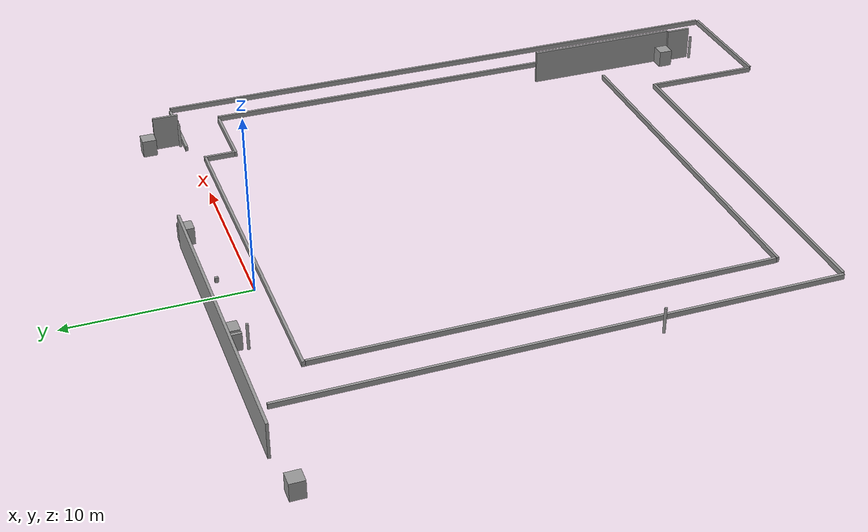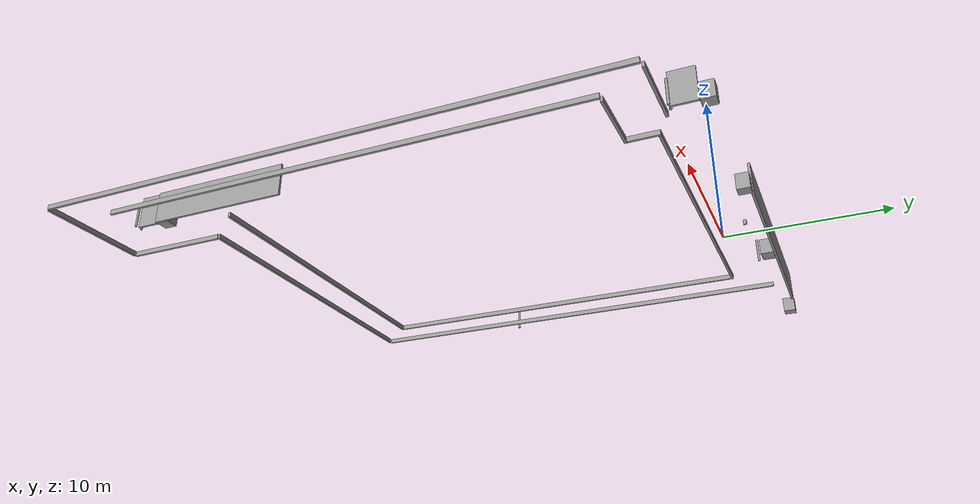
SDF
<?xml version='1.0'?>
<sdf version='1.6'>
  <model name='unit_box_map12'>
    <link name='link'>
      <pose frame=''>3.45997 -0.623895 0 0 -0 0</pose>
      <inertial>
        <mass>1</mass>
        <inertia>
          <ixx>0.166667</ixx>
          <ixy>0</ixy>
          <ixz>0</ixz>
          <iyy>0.166667</iyy>
          <iyz>0</iyz>
          <izz>0.166667</izz>
        </inertia>
        <pose frame=''>0 0 0 0 -0 0</pose>
      </inertial>
      <self_collide>0</self_collide>
      <kinematic>0</kinematic>
      <visual name='visual'>
        <geometry>
          <box>
            <size>20.4 0.15 0.3</size>
          </box>
        </geometry>
        <material>
          <script>
            <name>Gazebo/Grey</name>
            <uri>file://media/materials/scripts/gazebo.material</uri>
          </script>
          <ambient>0.3 0.3 0.3 1</ambient>
          <diffuse>0.7 0.7 0.7 1</diffuse>
          <specular>0.01 0.01 0.01 1</specular>
          <emissive>0 0 0 1</emissive>
          <shader type='vertex'>
            <normal_map>__default__</normal_map>
          </shader>
        </material>
        <pose frame=''>0 0 0 0 -0 0</pose>
        <cast_shadows>1</cast_shadows>
        <transparency>0</transparency>
      </visual>
      <collision name='collision'>
        <laser_retro>0</laser_retro>
        <max_contacts>10</max_contacts>
        <pose frame=''>0 0 0 0 -0 0</pose>
        <geometry>
          <box>
            <size>20.4 0.15 0.3</size>
          </box>
        </geometry>
        <surface>
          <friction>
            <ode>
              <mu>1</mu>
              <mu2>1</mu2>
              <fdir1>0 0 0</fdir1>
              <slip1>0</slip1>
              <slip2>0</slip2>
            </ode>
            <torsional>
              <coefficient>1</coefficient>
              <patch_radius>0</patch_radius>
              <surface_radius>0</surface_radius>
              <use_patch_radius>1</use_patch_radius>
              <ode>
                <slip>0</slip>
              </ode>
            </torsional>
          </friction>
          <bounce>
            <restitution_coefficient>0</restitution_coefficient>
            <threshold>1e+06</threshold>
          </bounce>
          <contact>
            <collide_without_contact>0</collide_without_contact>
            <collide_without_contact_bitmask>1</collide_without_contact_bitmask>
            <collide_bitmask>1</collide_bitmask>
            <ode>
              <soft_cfm>0</soft_cfm>
              <soft_erp>0.2</soft_erp>
              <kp>1e+13</kp>
              <kd>1</kd>
              <max_vel>0.01</max_vel>
              <min_depth>0</min_depth>
            </ode>
            <bullet>
              <split_impulse>1</split_impulse>
              <split_impulse_penetration_threshold>-0.01</split_impulse_penetration_threshold>
              <soft_cfm>0</soft_cfm>
              <soft_erp>0.2</soft_erp>
              <kp>1e+13</kp>
              <kd>1</kd>
            </bullet>
          </contact>
        </surface>
      </collision>
    </link>
    <link name='link_1'>
      <pose frame=''>5.64225 2.27249 0.5 0 -0 0</pose>
      <inertial>
        <mass>1</mass>
        <inertia>
          <ixx>0.166667</ixx>
          <ixy>0</ixy>
          <ixz>0</ixz>
          <iyy>0.166667</iyy>
          <iyz>0</iyz>
          <izz>0.166667</izz>
        </inertia>
        <pose frame=''>0 0 0 0 -0 0</pose>
      </inertial>
      <gravity>1</gravity>
      <self_collide>0</self_collide>
      <kinematic>0</kinematic>
      <visual name='visual'>
        <pose frame=''>0 0 0 0 -0 0</pose>
        <geometry>
          <box>
            <size>0.8 0.8 1</size>
          </box>
        </geometry>
        <material>
          <lighting>1</lighting>
          <script>
            <uri>file://media/materials/scripts/gazebo.material</uri>
            <name>Gazebo/Grey</name>
          </script>
          <ambient>0.3 0.3 0.3 1</ambient>
          <diffuse>0.7 0.7 0.7 1</diffuse>
          <specular>0.01 0.01 0.01 1</specular>
          <emissive>0 0 0 1</emissive>
          <shader type='vertex'>
            <normal_map>__default__</normal_map>
          </shader>
        </material>
        <cast_shadows>1</cast_shadows>
        <transparency>0</transparency>
      </visual>
      <collision name='collision'>
        <laser_retro>0</laser_retro>
        <max_contacts>10</max_contacts>
        <pose frame=''>0 0 0 0 -0 0</pose>
        <geometry>
          <box>
            <size>0.8 0.8 1</size>
          </box>
        </geometry>
        <surface>
          <friction>
            <ode>
              <mu>1</mu>
              <mu2>1</mu2>
              <fdir1>0 0 0</fdir1>
              <slip1>0</slip1>
              <slip2>0</slip2>
            </ode>
            <torsional>
              <coefficient>1</coefficient>
              <patch_radius>0</patch_radius>
              <surface_radius>0</surface_radius>
              <use_patch_radius>1</use_patch_radius>
              <ode>
                <slip>0</slip>
              </ode>
            </torsional>
          </friction>
          <bounce>
            <restitution_coefficient>0</restitution_coefficient>
            <threshold>1e+06</threshold>
          </bounce>
          <contact>
            <collide_without_contact>0</collide_without_contact>
            <collide_without_contact_bitmask>1</collide_without_contact_bitmask>
            <collide_bitmask>1</collide_bitmask>
            <ode>
              <soft_cfm>0</soft_cfm>
              <soft_erp>0.2</soft_erp>
              <kp>1e+13</kp>
              <kd>1</kd>
              <max_vel>0.01</max_vel>
              <min_depth>0</min_depth>
            </ode>
            <bullet>
              <split_impulse>1</split_impulse>
              <split_impulse_penetration_threshold>-0.01</split_impulse_penetration_threshold>
              <soft_cfm>0</soft_cfm>
              <soft_erp>0.2</soft_erp>
              <kp>1e+13</kp>
              <kd>1</kd>
            </bullet>
          </contact>
        </surface>
      </collision>
    </link>
    <link name='link_1_clone'>
      <pose frame=''>-3.92858 2.1759 0.5 0 -0 0</pose>
      <inertial>
        <mass>1</mass>
        <inertia>
          <ixx>0.166667</ixx>
          <ixy>0</ixy>
          <ixz>0</ixz>
          <iyy>0.166667</iyy>
          <iyz>0</iyz>
          <izz>0.166667</izz>
        </inertia>
        <pose frame=''>0 0 0 0 -0 0</pose>
      </inertial>
      <self_collide>0</self_collide>
      <kinematic>0</kinematic>
      <visual name='visual'>
        <pose frame=''>0 0 0 0 -0 0</pose>
        <geometry>
          <box>
            <size>0.8 0.8 1</size>
          </box>
        </geometry>
        <material>
          <lighting>1</lighting>
          <script>
            <uri>file://media/materials/scripts/gazebo.material</uri>
            <name>Gazebo/Grey</name>
          </script>
          <ambient>0.3 0.3 0.3 1</ambient>
          <diffuse>0.7 0.7 0.7 1</diffuse>
          <specular>0.01 0.01 0.01 1</specular>
          <emissive>0 0 0 1</emissive>
          <shader type='vertex'>
            <normal_map>__default__</normal_map>
          </shader>
        </material>
        <cast_shadows>1</cast_shadows>
        <transparency>0</transparency>
      </visual>
      <collision name='collision'>
        <laser_retro>0</laser_retro>
        <max_contacts>10</max_contacts>
        <pose frame=''>0 0 0 0 -0 0</pose>
        <geometry>
          <box>
            <size>0.8 0.8 1</size>
          </box>
        </geometry>
        <surface>
          <friction>
            <ode>
              <mu>1</mu>
              <mu2>1</mu2>
              <fdir1>0 0 0</fdir1>
              <slip1>0</slip1>
              <slip2>0</slip2>
            </ode>
            <torsional>
              <coefficient>1</coefficient>
              <patch_radius>0</patch_radius>
              <surface_radius>0</surface_radius>
              <use_patch_radius>1</use_patch_radius>
              <ode>
                <slip>0</slip>
              </ode>
            </torsional>
          </friction>
          <bounce>
            <restitution_coefficient>0</restitution_coefficient>
            <threshold>1e+06</threshold>
          </bounce>
          <contact>
            <collide_without_contact>0</collide_without_contact>
            <collide_without_contact_bitmask>1</collide_without_contact_bitmask>
            <collide_bitmask>1</collide_bitmask>
            <ode>
              <soft_cfm>0</soft_cfm>
              <soft_erp>0.2</soft_erp>
              <kp>1e+13</kp>
              <kd>1</kd>
              <max_vel>0.01</max_vel>
              <min_depth>0</min_depth>
            </ode>
            <bullet>
              <split_impulse>1</split_impulse>
              <split_impulse_penetration_threshold>-0.01</split_impulse_penetration_threshold>
              <soft_cfm>0</soft_cfm>
              <soft_erp>0.2</soft_erp>
              <kp>1e+13</kp>
              <kd>1</kd>
            </bullet>
          </contact>
        </surface>
      </collision>
    </link>
    <link name='link_1_clone_0'>
      <pose frame=''>15.5289 -30.814 0.5 0 -0 0</pose>
      <inertial>
        <mass>1</mass>
        <inertia>
          <ixx>0.166667</ixx>
          <ixy>0</ixy>
          <ixz>0</ixz>
          <iyy>0.166667</iyy>
          <iyz>0</iyz>
          <izz>0.166667</izz>
        </inertia>
        <pose frame=''>0 0 0 0 -0 0</pose>
      </inertial>
      <self_collide>0</self_collide>
      <kinematic>0</kinematic>
      <visual name='visual'>
        <pose frame=''>0 0 0 0 -0 0</pose>
        <geometry>
          <box>
            <size>0.8 0.8 1</size>
          </box>
        </geometry>
        <material>
          <lighting>1</lighting>
          <script>
            <uri>file://media/materials/scripts/gazebo.material</uri>
            <name>Gazebo/Grey</name>
          </script>
          <ambient>0.3 0.3 0.3 1</ambient>
          <diffuse>0.7 0.7 0.7 1</diffuse>
          <specular>0.01 0.01 0.01 1</specular>
          <emissive>0 0 0 1</emissive>
          <shader type='vertex'>
            <normal_map>__default__</normal_map>
          </shader>
        </material>
        <cast_shadows>1</cast_shadows>
        <transparency>0</transparency>
      </visual>
      <collision name='collision'>
        <laser_retro>0</laser_retro>
        <max_contacts>10</max_contacts>
        <pose frame=''>0 0 0 0 -0 0</pose>
        <geometry>
          <box>
            <size>0.8 0.8 1</size>
          </box>
        </geometry>
        <surface>
          <friction>
            <ode>
              <mu>1</mu>
              <mu2>1</mu2>
              <fdir1>0 0 0</fdir1>
              <slip1>0</slip1>
              <slip2>0</slip2>
            </ode>
            <torsional>
              <coefficient>1</coefficient>
              <patch_radius>0</patch_radius>
              <surface_radius>0</surface_radius>
              <use_patch_radius>1</use_patch_radius>
              <ode>
                <slip>0</slip>
              </ode>
            </torsional>
          </friction>
          <bounce>
            <restitution_coefficient>0</restitution_coefficient>
            <threshold>1e+06</threshold>
          </bounce>
          <contact>
            <collide_without_contact>0</collide_without_contact>
            <collide_without_contact_bitmask>1</collide_without_contact_bitmask>
            <collide_bitmask>1</collide_bitmask>
            <ode>
              <soft_cfm>0</soft_cfm>
              <soft_erp>0.2</soft_erp>
              <kp>1e+13</kp>
              <kd>1</kd>
              <max_vel>0.01</max_vel>
              <min_depth>0</min_depth>
            </ode>
            <bullet>
              <split_impulse>1</split_impulse>
              <split_impulse_penetration_threshold>-0.01</split_impulse_penetration_threshold>
              <soft_cfm>0</soft_cfm>
              <soft_erp>0.2</soft_erp>
              <kp>1e+13</kp>
              <kd>1</kd>
            </bullet>
          </contact>
        </surface>
      </collision>
    </link>
    <link name='link_1_clone_0_clone'>
      <pose frame=''>15.5381 2.27815 0.5 0 -0 0</pose>
      <inertial>
        <mass>1</mass>
        <inertia>
          <ixx>0.166667</ixx>
          <ixy>0</ixy>
          <ixz>0</ixz>
          <iyy>0.166667</iyy>
          <iyz>0</iyz>
          <izz>0.166667</izz>
        </inertia>
        <pose frame=''>0 0 0 0 -0 0</pose>
      </inertial>
      <self_collide>0</self_collide>
      <kinematic>0</kinematic>
      <visual name='visual'>
        <pose frame=''>0 0 0 0 -0 0</pose>
        <geometry>
          <box>
            <size>0.8 0.8 1</size>
          </box>
        </geometry>
        <material>
          <lighting>1</lighting>
          <script>
            <uri>file://media/materials/scripts/gazebo.material</uri>
            <name>Gazebo/Grey</name>
          </script>
          <ambient>0.3 0.3 0.3 1</ambient>
          <diffuse>0.7 0.7 0.7 1</diffuse>
          <specular>0.01 0.01 0.01 1</specular>
          <emissive>0 0 0 1</emissive>
          <shader type='vertex'>
            <normal_map>__default__</normal_map>
          </shader>
        </material>
        <cast_shadows>1</cast_shadows>
        <transparency>0</transparency>
      </visual>
      <collision name='collision'>
        <laser_retro>0</laser_retro>
        <max_contacts>10</max_contacts>
        <pose frame=''>0 0 0 0 -0 0</pose>
        <geometry>
          <box>
            <size>0.8 0.8 1</size>
          </box>
        </geometry>
        <surface>
          <friction>
            <ode>
              <mu>1</mu>
              <mu2>1</mu2>
              <fdir1>0 0 0</fdir1>
              <slip1>0</slip1>
              <slip2>0</slip2>
            </ode>
            <torsional>
              <coefficient>1</coefficient>
              <patch_radius>0</patch_radius>
              <surface_radius>0</surface_radius>
              <use_patch_radius>1</use_patch_radius>
              <ode>
                <slip>0</slip>
              </ode>
            </torsional>
          </friction>
          <bounce>
            <restitution_coefficient>0</restitution_coefficient>
            <threshold>1e+06</threshold>
          </bounce>
          <contact>
            <collide_without_contact>0</collide_without_contact>
            <collide_without_contact_bitmask>1</collide_without_contact_bitmask>
            <collide_bitmask>1</collide_bitmask>
            <ode>
              <soft_cfm>0</soft_cfm>
              <soft_erp>0.2</soft_erp>
              <kp>1e+13</kp>
              <kd>1</kd>
              <max_vel>0.01</max_vel>
              <min_depth>0</min_depth>
            </ode>
            <bullet>
              <split_impulse>1</split_impulse>
              <split_impulse_penetration_threshold>-0.01</split_impulse_penetration_threshold>
              <soft_cfm>0</soft_cfm>
              <soft_erp>0.2</soft_erp>
              <kp>1e+13</kp>
              <kd>1</kd>
            </bullet>
          </contact>
        </surface>
      </collision>
    </link>
    <link name='link_1_clone_clone'>
      <pose frame=''>-4.56641 2.17851 0.5 0 -0 0</pose>
      <inertial>
        <mass>0.216254</mass>
        <inertia>
          <ixx>0.0360423</ixx>
          <ixy>0</ixy>
          <ixz>0</ixz>
          <iyy>0.0188639</iyy>
          <iyz>0</iyz>
          <izz>0.0188639</izz>
        </inertia>
        <pose frame=''>0 0 0 0 -0 0</pose>
      </inertial>
      <self_collide>0</self_collide>
      <kinematic>0</kinematic>
      <gravity>1</gravity>
      <visual name='visual'>
        <pose frame=''>0 0 0 0 -0 0</pose>
        <geometry>
          <box>
            <size>0.173004 0.8 1</size>
          </box>
        </geometry>
        <material>
          <lighting>1</lighting>
          <script>
            <uri>file://media/materials/scripts/gazebo.material</uri>
            <name>Gazebo/Grey</name>
          </script>
          <ambient>0.3 0.3 0.3 1</ambient>
          <diffuse>0.7 0.7 0.7 1</diffuse>
          <specular>0.01 0.01 0.01 1</specular>
          <emissive>0 0 0 1</emissive>
          <shader type='vertex'>
            <normal_map>__default__</normal_map>
          </shader>
        </material>
        <cast_shadows>1</cast_shadows>
        <transparency>0</transparency>
      </visual>
      <collision name='collision'>
        <laser_retro>0</laser_retro>
        <max_contacts>10</max_contacts>
        <pose frame=''>0 0 0 0 -0 0</pose>
        <geometry>
          <box>
            <size>0.173004 0.8 1</size>
          </box>
        </geometry>
        <surface>
          <friction>
            <ode>
              <mu>1</mu>
              <mu2>1</mu2>
              <fdir1>0 0 0</fdir1>
              <slip1>0</slip1>
              <slip2>0</slip2>
            </ode>
            <torsional>
              <coefficient>1</coefficient>
              <patch_radius>0</patch_radius>
              <surface_radius>0</surface_radius>
              <use_patch_radius>1</use_patch_radius>
              <ode>
                <slip>0</slip>
              </ode>
            </torsional>
          </friction>
          <bounce>
            <restitution_coefficient>0</restitution_coefficient>
            <threshold>1e+06</threshold>
          </bounce>
          <contact>
            <collide_without_contact>0</collide_without_contact>
            <collide_without_contact_bitmask>1</collide_without_contact_bitmask>
            <collide_bitmask>1</collide_bitmask>
            <ode>
              <soft_cfm>0</soft_cfm>
              <soft_erp>0.2</soft_erp>
              <kp>1e+13</kp>
              <kd>1</kd>
              <max_vel>0.01</max_vel>
              <min_depth>0</min_depth>
            </ode>
            <bullet>
              <split_impulse>1</split_impulse>
              <split_impulse_penetration_threshold>-0.01</split_impulse_penetration_threshold>
              <soft_cfm>0</soft_cfm>
              <soft_erp>0.2</soft_erp>
              <kp>1e+13</kp>
              <kd>1</kd>
            </bullet>
          </contact>
        </surface>
      </collision>
    </link>
    <link name='link_1_clone_clone_0'>
      <pose frame=''>-15.389 2.17694 0.5 0 -0 0</pose>
      <inertial>
        <mass>1</mass>
        <inertia>
          <ixx>0.166667</ixx>
          <ixy>0</ixy>
          <ixz>0</ixz>
          <iyy>0.166667</iyy>
          <iyz>0</iyz>
          <izz>0.166667</izz>
        </inertia>
        <pose frame=''>0 0 0 0 -0 0</pose>
      </inertial>
      <self_collide>0</self_collide>
      <kinematic>0</kinematic>
      <visual name='visual'>
        <pose frame=''>0 0 0 0 -0 0</pose>
        <geometry>
          <box>
            <size>0.8 0.8 1</size>
          </box>
        </geometry>
        <material>
          <lighting>1</lighting>
          <script>
            <uri>file://media/materials/scripts/gazebo.material</uri>
            <name>Gazebo/Grey</name>
          </script>
          <ambient>0.3 0.3 0.3 1</ambient>
          <diffuse>0.7 0.7 0.7 1</diffuse>
          <specular>0.01 0.01 0.01 1</specular>
          <emissive>0 0 0 1</emissive>
          <shader type='vertex'>
            <normal_map>__default__</normal_map>
          </shader>
        </material>
        <cast_shadows>1</cast_shadows>
        <transparency>0</transparency>
      </visual>
      <collision name='collision'>
        <laser_retro>0</laser_retro>
        <max_contacts>10</max_contacts>
        <pose frame=''>0 0 0 0 -0 0</pose>
        <geometry>
          <box>
            <size>0.8 0.8 1</size>
          </box>
        </geometry>
        <surface>
          <friction>
            <ode>
              <mu>1</mu>
              <mu2>1</mu2>
              <fdir1>0 0 0</fdir1>
              <slip1>0</slip1>
              <slip2>0</slip2>
            </ode>
            <torsional>
              <coefficient>1</coefficient>
              <patch_radius>0</patch_radius>
              <surface_radius>0</surface_radius>
              <use_patch_radius>1</use_patch_radius>
              <ode>
                <slip>0</slip>
              </ode>
            </torsional>
          </friction>
          <bounce>
            <restitution_coefficient>0</restitution_coefficient>
            <threshold>1e+06</threshold>
          </bounce>
          <contact>
            <collide_without_contact>0</collide_without_contact>
            <collide_without_contact_bitmask>1</collide_without_contact_bitmask>
            <collide_bitmask>1</collide_bitmask>
            <ode>
              <soft_cfm>0</soft_cfm>
              <soft_erp>0.2</soft_erp>
              <kp>1e+13</kp>
              <kd>1</kd>
              <max_vel>0.01</max_vel>
              <min_depth>0</min_depth>
            </ode>
            <bullet>
              <split_impulse>1</split_impulse>
              <split_impulse_penetration_threshold>-0.01</split_impulse_penetration_threshold>
              <soft_cfm>0</soft_cfm>
              <soft_erp>0.2</soft_erp>
              <kp>1e+13</kp>
              <kd>1</kd>
            </bullet>
          </contact>
        </surface>
      </collision>
    </link>
    <link name='link_2'>
      <pose frame=''>-4.67409 1.51565 0.7539 0 -0 0</pose>
      <inertial>
        <mass>1</mass>
        <inertia>
          <ixx>0.145833</ixx>
          <ixy>0</ixy>
          <ixz>0</ixz>
          <iyy>0.145833</iyy>
          <iyz>0</iyz>
          <izz>0.125</izz>
        </inertia>
        <pose frame=''>0 0 0 0 -0 0</pose>
      </inertial>
      <gravity>1</gravity>
      <self_collide>0</self_collide>
      <kinematic>0</kinematic>
      <visual name='visual'>
        <pose frame=''>0 0 0 0 -0 0</pose>
        <geometry>
          <cylinder>
            <radius>0.075</radius>
            <length>1.5</length>
          </cylinder>
        </geometry>
        <material>
          <lighting>1</lighting>
          <script>
            <uri>file://media/materials/scripts/gazebo.material</uri>
            <name>Gazebo/Grey</name>
          </script>
          <ambient>0.3 0.3 0.3 1</ambient>
          <diffuse>0.7 0.7 0.7 1</diffuse>
          <specular>0.01 0.01 0.01 1</specular>
          <emissive>0 0 0 1</emissive>
          <shader type='vertex'>
            <normal_map>__default__</normal_map>
          </shader>
        </material>
        <cast_shadows>1</cast_shadows>
        <transparency>0</transparency>
      </visual>
      <collision name='collision'>
        <laser_retro>0</laser_retro>
        <max_contacts>10</max_contacts>
        <pose frame=''>0 0 0 0 -0 0</pose>
        <geometry>
          <cylinder>
            <radius>0.075</radius>
            <length>1.5</length>
          </cylinder>
        </geometry>
        <surface>
          <friction>
            <ode>
              <mu>1</mu>
              <mu2>1</mu2>
              <fdir1>0 0 0</fdir1>
              <slip1>0</slip1>
              <slip2>0</slip2>
            </ode>
            <torsional>
              <coefficient>1</coefficient>
              <patch_radius>0</patch_radius>
              <surface_radius>0</surface_radius>
              <use_patch_radius>1</use_patch_radius>
              <ode>
                <slip>0</slip>
              </ode>
            </torsional>
          </friction>
          <bounce>
            <restitution_coefficient>0</restitution_coefficient>
            <threshold>1e+06</threshold>
          </bounce>
          <contact>
            <collide_without_contact>0</collide_without_contact>
            <collide_without_contact_bitmask>1</collide_without_contact_bitmask>
            <collide_bitmask>1</collide_bitmask>
            <ode>
              <soft_cfm>0</soft_cfm>
              <soft_erp>0.2</soft_erp>
              <kp>1e+13</kp>
              <kd>1</kd>
              <max_vel>0.01</max_vel>
              <min_depth>0</min_depth>
            </ode>
            <bullet>
              <split_impulse>1</split_impulse>
              <split_impulse_penetration_threshold>-0.01</split_impulse_penetration_threshold>
              <soft_cfm>0</soft_cfm>
              <soft_erp>0.2</soft_erp>
              <kp>1e+13</kp>
              <kd>1</kd>
            </bullet>
          </contact>
        </surface>
      </collision>
    </link>
    <link name='link_2_clone'>
      <pose frame=''>16.0775 -32.7288 0.7539 0 -0 0</pose>
      <inertial>
        <mass>1</mass>
        <inertia>
          <ixx>0.145833</ixx>
          <ixy>0</ixy>
          <ixz>0</ixz>
          <iyy>0.145833</iyy>
          <iyz>0</iyz>
          <izz>0.125</izz>
        </inertia>
        <pose frame=''>0 0 0 0 -0 0</pose>
      </inertial>
      <self_collide>0</self_collide>
      <kinematic>0</kinematic>
      <visual name='visual'>
        <pose frame=''>0 0 0 0 -0 0</pose>
        <geometry>
          <cylinder>
            <radius>0.075</radius>
            <length>1.5</length>
          </cylinder>
        </geometry>
        <material>
          <lighting>1</lighting>
          <script>
            <uri>file://media/materials/scripts/gazebo.material</uri>
            <name>Gazebo/Grey</name>
          </script>
          <ambient>0.3 0.3 0.3 1</ambient>
          <diffuse>0.7 0.7 0.7 1</diffuse>
          <specular>0.01 0.01 0.01 1</specular>
          <emissive>0 0 0 1</emissive>
          <shader type='vertex'>
            <normal_map>__default__</normal_map>
          </shader>
        </material>
        <cast_shadows>1</cast_shadows>
        <transparency>0</transparency>
      </visual>
      <collision name='collision'>
        <laser_retro>0</laser_retro>
        <max_contacts>10</max_contacts>
        <pose frame=''>0 0 0 0 -0 0</pose>
        <geometry>
          <cylinder>
            <radius>0.075</radius>
            <length>1.5</length>
          </cylinder>
        </geometry>
        <surface>
          <friction>
            <ode>
              <mu>1</mu>
              <mu2>1</mu2>
              <fdir1>0 0 0</fdir1>
              <slip1>0</slip1>
              <slip2>0</slip2>
            </ode>
            <torsional>
              <coefficient>1</coefficient>
              <patch_radius>0</patch_radius>
              <surface_radius>0</surface_radius>
              <use_patch_radius>1</use_patch_radius>
              <ode>
                <slip>0</slip>
              </ode>
            </torsional>
          </friction>
          <bounce>
            <restitution_coefficient>0</restitution_coefficient>
            <threshold>1e+06</threshold>
          </bounce>
          <contact>
            <collide_without_contact>0</collide_without_contact>
            <collide_without_contact_bitmask>1</collide_without_contact_bitmask>
            <collide_bitmask>1</collide_bitmask>
            <ode>
              <soft_cfm>0</soft_cfm>
              <soft_erp>0.2</soft_erp>
              <kp>1e+13</kp>
              <kd>1</kd>
              <max_vel>0.01</max_vel>
              <min_depth>0</min_depth>
            </ode>
            <bullet>
              <split_impulse>1</split_impulse>
              <split_impulse_penetration_threshold>-0.01</split_impulse_penetration_threshold>
              <soft_cfm>0</soft_cfm>
              <soft_erp>0.2</soft_erp>
              <kp>1e+13</kp>
              <kd>1</kd>
            </bullet>
          </contact>
        </surface>
      </collision>
    </link>
    <link name='link_2_clone_0'>
      <pose frame=''>15.6074 -32.7433 0.7539 0 -0 0</pose>
      <inertial>
        <mass>1</mass>
        <inertia>
          <ixx>0.145833</ixx>
          <ixy>0</ixy>
          <ixz>0</ixz>
          <iyy>0.145833</iyy>
          <iyz>0</iyz>
          <izz>0.125</izz>
        </inertia>
        <pose frame=''>0 0 0 0 -0 0</pose>
      </inertial>
      <self_collide>0</self_collide>
      <kinematic>0</kinematic>
      <visual name='visual'>
        <pose frame=''>0 0 0 0 -0 0</pose>
        <geometry>
          <cylinder>
            <radius>0.075</radius>
            <length>1.5</length>
          </cylinder>
        </geometry>
        <material>
          <lighting>1</lighting>
          <script>
            <uri>file://media/materials/scripts/gazebo.material</uri>
            <name>Gazebo/Grey</name>
          </script>
          <ambient>0.3 0.3 0.3 1</ambient>
          <diffuse>0.7 0.7 0.7 1</diffuse>
          <specular>0.01 0.01 0.01 1</specular>
          <emissive>0 0 0 1</emissive>
          <shader type='vertex'>
            <normal_map>__default__</normal_map>
          </shader>
        </material>
        <cast_shadows>1</cast_shadows>
        <transparency>0</transparency>
      </visual>
      <collision name='collision'>
        <laser_retro>0</laser_retro>
        <max_contacts>10</max_contacts>
        <pose frame=''>0 0 0 0 -0 0</pose>
        <geometry>
          <cylinder>
            <radius>0.075</radius>
            <length>1.5</length>
          </cylinder>
        </geometry>
        <surface>
          <friction>
            <ode>
              <mu>1</mu>
              <mu2>1</mu2>
              <fdir1>0 0 0</fdir1>
              <slip1>0</slip1>
              <slip2>0</slip2>
            </ode>
            <torsional>
              <coefficient>1</coefficient>
              <patch_radius>0</patch_radius>
              <surface_radius>0</surface_radius>
              <use_patch_radius>1</use_patch_radius>
              <ode>
                <slip>0</slip>
              </ode>
            </torsional>
          </friction>
          <bounce>
            <restitution_coefficient>0</restitution_coefficient>
            <threshold>1e+06</threshold>
          </bounce>
          <contact>
            <collide_without_contact>0</collide_without_contact>
            <collide_without_contact_bitmask>1</collide_without_contact_bitmask>
            <collide_bitmask>1</collide_bitmask>
            <ode>
              <soft_cfm>0</soft_cfm>
              <soft_erp>0.2</soft_erp>
              <kp>1e+13</kp>
              <kd>1</kd>
              <max_vel>0.01</max_vel>
              <min_depth>0</min_depth>
            </ode>
            <bullet>
              <split_impulse>1</split_impulse>
              <split_impulse_penetration_threshold>-0.01</split_impulse_penetration_threshold>
              <soft_cfm>0</soft_cfm>
              <soft_erp>0.2</soft_erp>
              <kp>1e+13</kp>
              <kd>1</kd>
            </bullet>
          </contact>
        </surface>
      </collision>
    </link>
    <link name='link_2_clone_clone'>
      <pose frame=''>16.0812 0.409793 0.7539 0 -0 0</pose>
      <inertial>
        <mass>1</mass>
        <inertia>
          <ixx>0.145833</ixx>
          <ixy>0</ixy>
          <ixz>0</ixz>
          <iyy>0.145833</iyy>
          <iyz>0</iyz>
          <izz>0.125</izz>
        </inertia>
        <pose frame=''>0 0 0 0 -0 0</pose>
      </inertial>
      <self_collide>0</self_collide>
      <kinematic>0</kinematic>
      <visual name='visual'>
        <pose frame=''>0 0 0 0 -0 0</pose>
        <geometry>
          <cylinder>
            <radius>0.075</radius>
            <length>1.5</length>
          </cylinder>
        </geometry>
        <material>
          <lighting>1</lighting>
          <script>
            <uri>file://media/materials/scripts/gazebo.material</uri>
            <name>Gazebo/Grey</name>
          </script>
          <ambient>0.3 0.3 0.3 1</ambient>
          <diffuse>0.7 0.7 0.7 1</diffuse>
          <specular>0.01 0.01 0.01 1</specular>
          <emissive>0 0 0 1</emissive>
          <shader type='vertex'>
            <normal_map>__default__</normal_map>
          </shader>
        </material>
        <cast_shadows>1</cast_shadows>
        <transparency>0</transparency>
      </visual>
      <collision name='collision'>
        <laser_retro>0</laser_retro>
        <max_contacts>10</max_contacts>
        <pose frame=''>0 0 0 0 -0 0</pose>
        <geometry>
          <cylinder>
            <radius>0.075</radius>
            <length>1.5</length>
          </cylinder>
        </geometry>
        <surface>
          <friction>
            <ode>
              <mu>1</mu>
              <mu2>1</mu2>
              <fdir1>0 0 0</fdir1>
              <slip1>0</slip1>
              <slip2>0</slip2>
            </ode>
            <torsional>
              <coefficient>1</coefficient>
              <patch_radius>0</patch_radius>
              <surface_radius>0</surface_radius>
              <use_patch_radius>1</use_patch_radius>
              <ode>
                <slip>0</slip>
              </ode>
            </torsional>
          </friction>
          <bounce>
            <restitution_coefficient>0</restitution_coefficient>
            <threshold>1e+06</threshold>
          </bounce>
          <contact>
            <collide_without_contact>0</collide_without_contact>
            <collide_without_contact_bitmask>1</collide_without_contact_bitmask>
            <collide_bitmask>1</collide_bitmask>
            <ode>
              <soft_cfm>0</soft_cfm>
              <soft_erp>0.2</soft_erp>
              <kp>1e+13</kp>
              <kd>1</kd>
              <max_vel>0.01</max_vel>
              <min_depth>0</min_depth>
            </ode>
            <bullet>
              <split_impulse>1</split_impulse>
              <split_impulse_penetration_threshold>-0.01</split_impulse_penetration_threshold>
              <soft_cfm>0</soft_cfm>
              <soft_erp>0.2</soft_erp>
              <kp>1e+13</kp>
              <kd>1</kd>
            </bullet>
          </contact>
        </surface>
      </collision>
    </link>
    <link name='link_2_clone_clone_0'>
      <pose frame=''>15.6338 0.415175 0.7539 0 -0 0</pose>
      <inertial>
        <mass>1</mass>
        <inertia>
          <ixx>0.145833</ixx>
          <ixy>0</ixy>
          <ixz>0</ixz>
          <iyy>0.145833</iyy>
          <iyz>0</iyz>
          <izz>0.125</izz>
        </inertia>
        <pose frame=''>0 0 0 0 -0 0</pose>
      </inertial>
      <self_collide>0</self_collide>
      <kinematic>0</kinematic>
      <visual name='visual'>
        <pose frame=''>0 0 0 0 -0 0</pose>
        <geometry>
          <cylinder>
            <radius>0.075</radius>
            <length>1.5</length>
          </cylinder>
        </geometry>
        <material>
          <lighting>1</lighting>
          <script>
            <uri>file://media/materials/scripts/gazebo.material</uri>
            <name>Gazebo/Grey</name>
          </script>
          <ambient>0.3 0.3 0.3 1</ambient>
          <diffuse>0.7 0.7 0.7 1</diffuse>
          <specular>0.01 0.01 0.01 1</specular>
          <emissive>0 0 0 1</emissive>
          <shader type='vertex'>
            <normal_map>__default__</normal_map>
          </shader>
        </material>
        <cast_shadows>1</cast_shadows>
        <transparency>0</transparency>
      </visual>
      <collision name='collision'>
        <laser_retro>0</laser_retro>
        <max_contacts>10</max_contacts>
        <pose frame=''>0 0 0 0 -0 0</pose>
        <geometry>
          <cylinder>
            <radius>0.075</radius>
            <length>1.5</length>
          </cylinder>
        </geometry>
        <surface>
          <friction>
            <ode>
              <mu>1</mu>
              <mu2>1</mu2>
              <fdir1>0 0 0</fdir1>
              <slip1>0</slip1>
              <slip2>0</slip2>
            </ode>
            <torsional>
              <coefficient>1</coefficient>
              <patch_radius>0</patch_radius>
              <surface_radius>0</surface_radius>
              <use_patch_radius>1</use_patch_radius>
              <ode>
                <slip>0</slip>
              </ode>
            </torsional>
          </friction>
          <bounce>
            <restitution_coefficient>0</restitution_coefficient>
            <threshold>1e+06</threshold>
          </bounce>
          <contact>
            <collide_without_contact>0</collide_without_contact>
            <collide_without_contact_bitmask>1</collide_without_contact_bitmask>
            <collide_bitmask>1</collide_bitmask>
            <ode>
              <soft_cfm>0</soft_cfm>
              <soft_erp>0.2</soft_erp>
              <kp>1e+13</kp>
              <kd>1</kd>
              <max_vel>0.01</max_vel>
              <min_depth>0</min_depth>
            </ode>
            <bullet>
              <split_impulse>1</split_impulse>
              <split_impulse_penetration_threshold>-0.01</split_impulse_penetration_threshold>
              <soft_cfm>0</soft_cfm>
              <soft_erp>0.2</soft_erp>
              <kp>1e+13</kp>
              <kd>1</kd>
            </bullet>
          </contact>
        </surface>
      </collision>
    </link>
    <link name='link_2_clone_clone_0_clone'>
      <pose frame=''>-10.3926 -17.9729 0.7539 0 -0 0</pose>
      <inertial>
        <mass>1</mass>
        <inertia>
          <ixx>0.145833</ixx>
          <ixy>0</ixy>
          <ixz>0</ixz>
          <iyy>0.145833</iyy>
          <iyz>0</iyz>
          <izz>0.125</izz>
        </inertia>
        <pose frame=''>0 0 0 0 -0 0</pose>
      </inertial>
      <self_collide>0</self_collide>
      <kinematic>0</kinematic>
      <visual name='visual'>
        <pose frame=''>0 0 0 0 -0 0</pose>
        <geometry>
          <cylinder>
            <radius>0.075</radius>
            <length>1.5</length>
          </cylinder>
        </geometry>
        <material>
          <lighting>1</lighting>
          <script>
            <uri>file://media/materials/scripts/gazebo.material</uri>
            <name>Gazebo/Grey</name>
          </script>
          <ambient>0.3 0.3 0.3 1</ambient>
          <diffuse>0.7 0.7 0.7 1</diffuse>
          <specular>0.01 0.01 0.01 1</specular>
          <emissive>0 0 0 1</emissive>
          <shader type='vertex'>
            <normal_map>__default__</normal_map>
          </shader>
        </material>
        <cast_shadows>1</cast_shadows>
        <transparency>0</transparency>
      </visual>
      <collision name='collision'>
        <laser_retro>0</laser_retro>
        <max_contacts>10</max_contacts>
        <pose frame=''>0 0 0 0 -0 0</pose>
        <geometry>
          <cylinder>
            <radius>0.075</radius>
            <length>1.5</length>
          </cylinder>
        </geometry>
        <surface>
          <friction>
            <ode>
              <mu>1</mu>
              <mu2>1</mu2>
              <fdir1>0 0 0</fdir1>
              <slip1>0</slip1>
              <slip2>0</slip2>
            </ode>
            <torsional>
              <coefficient>1</coefficient>
              <patch_radius>0</patch_radius>
              <surface_radius>0</surface_radius>
              <use_patch_radius>1</use_patch_radius>
              <ode>
                <slip>0</slip>
              </ode>
            </torsional>
          </friction>
          <bounce>
            <restitution_coefficient>0</restitution_coefficient>
            <threshold>1e+06</threshold>
          </bounce>
          <contact>
            <collide_without_contact>0</collide_without_contact>
            <collide_without_contact_bitmask>1</collide_without_contact_bitmask>
            <collide_bitmask>1</collide_bitmask>
            <ode>
              <soft_cfm>0</soft_cfm>
              <soft_erp>0.2</soft_erp>
              <kp>1e+13</kp>
              <kd>1</kd>
              <max_vel>0.01</max_vel>
              <min_depth>0</min_depth>
            </ode>
            <bullet>
              <split_impulse>1</split_impulse>
              <split_impulse_penetration_threshold>-0.01</split_impulse_penetration_threshold>
              <soft_cfm>0</soft_cfm>
              <soft_erp>0.2</soft_erp>
              <kp>1e+13</kp>
              <kd>1</kd>
            </bullet>
          </contact>
        </surface>
      </collision>
    </link>
    <link name='link_clone'>
      <pose frame=''>-3.76019 2.65371 0.997263 0 -0 0</pose>
      <inertial>
        <mass>1</mass>
        <inertia>
          <ixx>0.166667</ixx>
          <ixy>0</ixy>
          <ixz>0</ixz>
          <iyy>0.166667</iyy>
          <iyz>0</iyz>
          <izz>0.166667</izz>
        </inertia>
        <pose frame=''>0 0 0 0 -0 0</pose>
      </inertial>
      <self_collide>0</self_collide>
      <kinematic>0</kinematic>
      <gravity>1</gravity>
      <visual name='visual'>
        <geometry>
          <box>
            <size>18 0.15 2</size>
          </box>
        </geometry>
        <material>
          <script>
            <name>Gazebo/Grey</name>
            <uri>file://media/materials/scripts/gazebo.material</uri>
          </script>
          <ambient>0.3 0.3 0.3 1</ambient>
          <diffuse>0.7 0.7 0.7 1</diffuse>
          <specular>0.01 0.01 0.01 1</specular>
          <emissive>0 0 0 1</emissive>
          <shader type='vertex'>
            <normal_map>__default__</normal_map>
          </shader>
        </material>
        <pose frame=''>0 0 0 0 -0 0</pose>
        <cast_shadows>1</cast_shadows>
        <transparency>0</transparency>
      </visual>
      <collision name='collision'>
        <laser_retro>0</laser_retro>
        <max_contacts>10</max_contacts>
        <pose frame=''>0 0 0 0 -0 0</pose>
        <geometry>
          <box>
            <size>18 0.15 2</size>
          </box>
        </geometry>
        <surface>
          <friction>
            <ode>
              <mu>1</mu>
              <mu2>1</mu2>
              <fdir1>0 0 0</fdir1>
              <slip1>0</slip1>
              <slip2>0</slip2>
            </ode>
            <torsional>
              <coefficient>1</coefficient>
              <patch_radius>0</patch_radius>
              <surface_radius>0</surface_radius>
              <use_patch_radius>1</use_patch_radius>
              <ode>
                <slip>0</slip>
              </ode>
            </torsional>
          </friction>
          <bounce>
            <restitution_coefficient>0</restitution_coefficient>
            <threshold>1e+06</threshold>
          </bounce>
          <contact>
            <collide_without_contact>0</collide_without_contact>
            <collide_without_contact_bitmask>1</collide_without_contact_bitmask>
            <collide_bitmask>1</collide_bitmask>
            <ode>
              <soft_cfm>0</soft_cfm>
              <soft_erp>0.2</soft_erp>
              <kp>1e+13</kp>
              <kd>1</kd>
              <max_vel>0.01</max_vel>
              <min_depth>0</min_depth>
            </ode>
            <bullet>
              <split_impulse>1</split_impulse>
              <split_impulse_penetration_threshold>-0.01</split_impulse_penetration_threshold>
              <soft_cfm>0</soft_cfm>
              <soft_erp>0.2</soft_erp>
              <kp>1e+13</kp>
              <kd>1</kd>
            </bullet>
          </contact>
        </surface>
      </collision>
    </link>
    <link name='link_clone_0_clone'>
      <pose frame=''>1.60516 1.62127 0 0 -0 1.5707</pose>
      <inertial>
        <mass>1</mass>
        <inertia>
          <ixx>0.166667</ixx>
          <ixy>0</ixy>
          <ixz>0</ixz>
          <iyy>0.166667</iyy>
          <iyz>0</iyz>
          <izz>0.166667</izz>
        </inertia>
        <pose frame=''>0 0 0 0 -0 0</pose>
      </inertial>
      <self_collide>0</self_collide>
      <kinematic>0</kinematic>
      <visual name='visual'>
        <geometry>
          <box>
            <size>0.2 0.15 0.3</size>
          </box>
        </geometry>
        <material>
          <script>
            <name>Gazebo/Grey</name>
            <uri>file://media/materials/scripts/gazebo.material</uri>
          </script>
          <ambient>0.3 0.3 0.3 1</ambient>
          <diffuse>0.7 0.7 0.7 1</diffuse>
          <specular>0.01 0.01 0.01 1</specular>
          <emissive>0 0 0 1</emissive>
          <shader type='vertex'>
            <normal_map>__default__</normal_map>
          </shader>
        </material>
        <pose frame=''>0 0 0 0 -0 0</pose>
        <cast_shadows>1</cast_shadows>
        <transparency>0</transparency>
      </visual>
      <collision name='collision'>
        <laser_retro>0</laser_retro>
        <max_contacts>10</max_contacts>
        <pose frame=''>0 0 0 0 -0 0</pose>
        <geometry>
          <box>
            <size>0.2 0.15 0.3</size>
          </box>
        </geometry>
        <surface>
          <friction>
            <ode>
              <mu>1</mu>
              <mu2>1</mu2>
              <fdir1>0 0 0</fdir1>
              <slip1>0</slip1>
              <slip2>0</slip2>
            </ode>
            <torsional>
              <coefficient>1</coefficient>
              <patch_radius>0</patch_radius>
              <surface_radius>0</surface_radius>
              <use_patch_radius>1</use_patch_radius>
              <ode>
                <slip>0</slip>
              </ode>
            </torsional>
          </friction>
          <bounce>
            <restitution_coefficient>0</restitution_coefficient>
            <threshold>1e+06</threshold>
          </bounce>
          <contact>
            <collide_without_contact>0</collide_without_contact>
            <collide_without_contact_bitmask>1</collide_without_contact_bitmask>
            <collide_bitmask>1</collide_bitmask>
            <ode>
              <soft_cfm>0</soft_cfm>
              <soft_erp>0.2</soft_erp>
              <kp>1e+13</kp>
              <kd>1</kd>
              <max_vel>0.01</max_vel>
              <min_depth>0</min_depth>
            </ode>
            <bullet>
              <split_impulse>1</split_impulse>
              <split_impulse_penetration_threshold>-0.01</split_impulse_penetration_threshold>
              <soft_cfm>0</soft_cfm>
              <soft_erp>0.2</soft_erp>
              <kp>1e+13</kp>
              <kd>1</kd>
            </bullet>
          </contact>
        </surface>
      </collision>
    </link>
    <link name='link_clone_0_clone_0'>
      <pose frame=''>4.18838 -26.4536 0 0 -0 0</pose>
      <inertial>
        <mass>1</mass>
        <inertia>
          <ixx>0.166667</ixx>
          <ixy>0</ixy>
          <ixz>0</ixz>
          <iyy>0.166667</iyy>
          <iyz>0</iyz>
          <izz>0.166667</izz>
        </inertia>
        <pose frame=''>0 0 0 0 -0 0</pose>
      </inertial>
      <self_collide>0</self_collide>
      <kinematic>0</kinematic>
      <visual name='visual'>
        <geometry>
          <box>
            <size>21.8 0.15 0.3</size>
          </box>
        </geometry>
        <material>
          <script>
            <name>Gazebo/Grey</name>
            <uri>file://media/materials/scripts/gazebo.material</uri>
          </script>
          <ambient>0.3 0.3 0.3 1</ambient>
          <diffuse>0.7 0.7 0.7 1</diffuse>
          <specular>0.01 0.01 0.01 1</specular>
          <emissive>0 0 0 1</emissive>
          <shader type='vertex'>
            <normal_map>__default__</normal_map>
          </shader>
        </material>
        <pose frame=''>0 0 0 0 -0 0</pose>
        <cast_shadows>1</cast_shadows>
        <transparency>0</transparency>
      </visual>
      <collision name='collision'>
        <laser_retro>0</laser_retro>
        <max_contacts>10</max_contacts>
        <pose frame=''>0 0 0 0 -0 0</pose>
        <geometry>
          <box>
            <size>21.8 0.15 0.3</size>
          </box>
        </geometry>
        <surface>
          <friction>
            <ode>
              <mu>1</mu>
              <mu2>1</mu2>
              <fdir1>0 0 0</fdir1>
              <slip1>0</slip1>
              <slip2>0</slip2>
            </ode>
            <torsional>
              <coefficient>1</coefficient>
              <patch_radius>0</patch_radius>
              <surface_radius>0</surface_radius>
              <use_patch_radius>1</use_patch_radius>
              <ode>
                <slip>0</slip>
              </ode>
            </torsional>
          </friction>
          <bounce>
            <restitution_coefficient>0</restitution_coefficient>
            <threshold>1e+06</threshold>
          </bounce>
          <contact>
            <collide_without_contact>0</collide_without_contact>
            <collide_without_contact_bitmask>1</collide_without_contact_bitmask>
            <collide_bitmask>1</collide_bitmask>
            <ode>
              <soft_cfm>0</soft_cfm>
              <soft_erp>0.2</soft_erp>
              <kp>1e+13</kp>
              <kd>1</kd>
              <max_vel>0.01</max_vel>
              <min_depth>0</min_depth>
            </ode>
            <bullet>
              <split_impulse>1</split_impulse>
              <split_impulse_penetration_threshold>-0.01</split_impulse_penetration_threshold>
              <soft_cfm>0</soft_cfm>
              <soft_erp>0.2</soft_erp>
              <kp>1e+13</kp>
              <kd>1</kd>
            </bullet>
          </contact>
        </surface>
      </collision>
    </link>
    <link name='link_clone_0_clone_0_clone_clone'>
      <pose frame=''>15.7693 -2.40821 0 0 -0 0</pose>
      <inertial>
        <mass>1</mass>
        <inertia>
          <ixx>0.166667</ixx>
          <ixy>0</ixy>
          <ixz>0</ixz>
          <iyy>0.166667</iyy>
          <iyz>0</iyz>
          <izz>0.166667</izz>
        </inertia>
        <pose frame=''>0 0 0 0 -0 0</pose>
      </inertial>
      <self_collide>0</self_collide>
      <kinematic>0</kinematic>
      <visual name='visual'>
        <geometry>
          <box>
            <size>4.21 0.15 0.3</size>
          </box>
        </geometry>
        <material>
          <script>
            <name>Gazebo/Grey</name>
            <uri>file://media/materials/scripts/gazebo.material</uri>
          </script>
          <ambient>0.3 0.3 0.3 1</ambient>
          <diffuse>0.7 0.7 0.7 1</diffuse>
          <specular>0.01 0.01 0.01 1</specular>
          <emissive>0 0 0 1</emissive>
          <shader type='vertex'>
            <normal_map>__default__</normal_map>
          </shader>
        </material>
        <pose frame=''>0 0 0 0 -0 0</pose>
        <cast_shadows>1</cast_shadows>
        <transparency>0</transparency>
      </visual>
      <collision name='collision'>
        <laser_retro>0</laser_retro>
        <max_contacts>10</max_contacts>
        <pose frame=''>0 0 0 0 -0 0</pose>
        <geometry>
          <box>
            <size>4.21 0.15 0.3</size>
          </box>
        </geometry>
        <surface>
          <friction>
            <ode>
              <mu>1</mu>
              <mu2>1</mu2>
              <fdir1>0 0 0</fdir1>
              <slip1>0</slip1>
              <slip2>0</slip2>
            </ode>
            <torsional>
              <coefficient>1</coefficient>
              <patch_radius>0</patch_radius>
              <surface_radius>0</surface_radius>
              <use_patch_radius>1</use_patch_radius>
              <ode>
                <slip>0</slip>
              </ode>
            </torsional>
          </friction>
          <bounce>
            <restitution_coefficient>0</restitution_coefficient>
            <threshold>1e+06</threshold>
          </bounce>
          <contact>
            <collide_without_contact>0</collide_without_contact>
            <collide_without_contact_bitmask>1</collide_without_contact_bitmask>
            <collide_bitmask>1</collide_bitmask>
            <ode>
              <soft_cfm>0</soft_cfm>
              <soft_erp>0.2</soft_erp>
              <kp>1e+13</kp>
              <kd>1</kd>
              <max_vel>0.01</max_vel>
              <min_depth>0</min_depth>
            </ode>
            <bullet>
              <split_impulse>1</split_impulse>
              <split_impulse_penetration_threshold>-0.01</split_impulse_penetration_threshold>
              <soft_cfm>0</soft_cfm>
              <soft_erp>0.2</soft_erp>
              <kp>1e+13</kp>
              <kd>1</kd>
            </bullet>
          </contact>
        </surface>
      </collision>
    </link>
    <link name='link_clone_0_clone_0_clone_clone_clone'>
      <pose frame=''>17.5173 0.14167 0 0 -0 0</pose>
      <inertial>
        <mass>0.716393</mass>
        <inertia>
          <ixx>0.119399</ixx>
          <ixy>0</ixy>
          <ixz>0</ixz>
          <iyy>0.0903386</iyy>
          <iyz>0</iyz>
          <izz>0.0903386</izz>
        </inertia>
        <pose frame=''>0 0 0 0 -0 0</pose>
      </inertial>
      <self_collide>0</self_collide>
      <kinematic>0</kinematic>
      <visual name='visual'>
        <geometry>
          <box>
            <size>4.53477 0.15 0.3</size>
          </box>
        </geometry>
        <material>
          <script>
            <name>Gazebo/Grey</name>
            <uri>file://media/materials/scripts/gazebo.material</uri>
          </script>
          <ambient>0.3 0.3 0.3 1</ambient>
          <diffuse>0.7 0.7 0.7 1</diffuse>
          <specular>0.01 0.01 0.01 1</specular>
          <emissive>0 0 0 1</emissive>
          <shader type='vertex'>
            <normal_map>__default__</normal_map>
          </shader>
        </material>
        <pose frame=''>0 0 0 0 -0 0</pose>
        <cast_shadows>1</cast_shadows>
        <transparency>0</transparency>
      </visual>
      <collision name='collision'>
        <laser_retro>0</laser_retro>
        <max_contacts>10</max_contacts>
        <pose frame=''>0 0 0 0 -0 0</pose>
        <geometry>
          <box>
            <size>4.53477 0.15 0.3</size>
          </box>
        </geometry>
        <surface>
          <friction>
            <ode>
              <mu>1</mu>
              <mu2>1</mu2>
              <fdir1>0 0 0</fdir1>
              <slip1>0</slip1>
              <slip2>0</slip2>
            </ode>
            <torsional>
              <coefficient>1</coefficient>
              <patch_radius>0</patch_radius>
              <surface_radius>0</surface_radius>
              <use_patch_radius>1</use_patch_radius>
              <ode>
                <slip>0</slip>
              </ode>
            </torsional>
          </friction>
          <bounce>
            <restitution_coefficient>0</restitution_coefficient>
            <threshold>1e+06</threshold>
          </bounce>
          <contact>
            <collide_without_contact>0</collide_without_contact>
            <collide_without_contact_bitmask>1</collide_without_contact_bitmask>
            <collide_bitmask>1</collide_bitmask>
            <ode>
              <soft_cfm>0</soft_cfm>
              <soft_erp>0.2</soft_erp>
              <kp>1e+13</kp>
              <kd>1</kd>
              <max_vel>0.01</max_vel>
              <min_depth>0</min_depth>
            </ode>
            <bullet>
              <split_impulse>1</split_impulse>
              <split_impulse_penetration_threshold>-0.01</split_impulse_penetration_threshold>
              <soft_cfm>0</soft_cfm>
              <soft_erp>0.2</soft_erp>
              <kp>1e+13</kp>
              <kd>1</kd>
            </bullet>
          </contact>
        </surface>
      </collision>
    </link>
    <link name='link_clone_0_clone_0_clone_clone_clone_0'>
      <pose frame=''>16.4921 -35.6942 0 0 -0 0</pose>
      <inertial>
        <mass>1</mass>
        <inertia>
          <ixx>0.166667</ixx>
          <ixy>0</ixy>
          <ixz>0</ixz>
          <iyy>0.166667</iyy>
          <iyz>0</iyz>
          <izz>0.166667</izz>
        </inertia>
        <pose frame=''>0 0 0 0 -0 0</pose>
      </inertial>
      <self_collide>0</self_collide>
      <kinematic>0</kinematic>
      <visual name='visual'>
        <geometry>
          <box>
            <size>7.1 0.15 0.3</size>
          </box>
        </geometry>
        <material>
          <script>
            <name>Gazebo/Grey</name>
            <uri>file://media/materials/scripts/gazebo.material</uri>
          </script>
          <ambient>0.3 0.3 0.3 1</ambient>
          <diffuse>0.7 0.7 0.7 1</diffuse>
          <specular>0.01 0.01 0.01 1</specular>
          <emissive>0 0 0 1</emissive>
          <shader type='vertex'>
            <normal_map>__default__</normal_map>
          </shader>
        </material>
        <pose frame=''>0 0 0 0 -0 0</pose>
        <cast_shadows>1</cast_shadows>
        <transparency>0</transparency>
      </visual>
      <collision name='collision'>
        <laser_retro>0</laser_retro>
        <max_contacts>10</max_contacts>
        <pose frame=''>0 0 0 0 -0 0</pose>
        <geometry>
          <box>
            <size>7.1 0.15 0.3</size>
          </box>
        </geometry>
        <surface>
          <friction>
            <ode>
              <mu>1</mu>
              <mu2>1</mu2>
              <fdir1>0 0 0</fdir1>
              <slip1>0</slip1>
              <slip2>0</slip2>
            </ode>
            <torsional>
              <coefficient>1</coefficient>
              <patch_radius>0</patch_radius>
              <surface_radius>0</surface_radius>
              <use_patch_radius>1</use_patch_radius>
              <ode>
                <slip>0</slip>
              </ode>
            </torsional>
          </friction>
          <bounce>
            <restitution_coefficient>0</restitution_coefficient>
            <threshold>1e+06</threshold>
          </bounce>
          <contact>
            <collide_without_contact>0</collide_without_contact>
            <collide_without_contact_bitmask>1</collide_without_contact_bitmask>
            <collide_bitmask>1</collide_bitmask>
            <ode>
              <soft_cfm>0</soft_cfm>
              <soft_erp>0.2</soft_erp>
              <kp>1e+13</kp>
              <kd>1</kd>
              <max_vel>0.01</max_vel>
              <min_depth>0</min_depth>
            </ode>
            <bullet>
              <split_impulse>1</split_impulse>
              <split_impulse_penetration_threshold>-0.01</split_impulse_penetration_threshold>
              <soft_cfm>0</soft_cfm>
              <soft_erp>0.2</soft_erp>
              <kp>1e+13</kp>
              <kd>1</kd>
            </bullet>
          </contact>
        </surface>
      </collision>
    </link>
    <link name='link_clone_0_clone_clone'>
      <pose frame=''>-9.18362 -13.5485 0 0 -0 1.5707</pose>
      <inertial>
        <mass>1</mass>
        <inertia>
          <ixx>0.166667</ixx>
          <ixy>0</ixy>
          <ixz>0</ixz>
          <iyy>0.166667</iyy>
          <iyz>0</iyz>
          <izz>0.166667</izz>
        </inertia>
        <pose frame=''>0 0 0 0 -0 0</pose>
      </inertial>
      <self_collide>0</self_collide>
      <kinematic>0</kinematic>
      <visual name='visual'>
        <geometry>
          <box>
            <size>30.7 0.15 0.3</size>
          </box>
        </geometry>
        <material>
          <script>
            <name>Gazebo/Grey</name>
            <uri>file://media/materials/scripts/gazebo.material</uri>
          </script>
          <ambient>0.3 0.3 0.3 1</ambient>
          <diffuse>0.7 0.7 0.7 1</diffuse>
          <specular>0.01 0.01 0.01 1</specular>
          <emissive>0 0 0 1</emissive>
          <shader type='vertex'>
            <normal_map>__default__</normal_map>
          </shader>
        </material>
        <pose frame=''>0 0 0 0 -0 0</pose>
        <cast_shadows>1</cast_shadows>
        <transparency>0</transparency>
      </visual>
      <collision name='collision'>
        <laser_retro>0</laser_retro>
        <max_contacts>10</max_contacts>
        <pose frame=''>0 0 0 0 -0 0</pose>
        <geometry>
          <box>
            <size>30.7 0.15 0.3</size>
          </box>
        </geometry>
        <surface>
          <friction>
            <ode>
              <mu>1</mu>
              <mu2>1</mu2>
              <fdir1>0 0 0</fdir1>
              <slip1>0</slip1>
              <slip2>0</slip2>
            </ode>
            <torsional>
              <coefficient>1</coefficient>
              <patch_radius>0</patch_radius>
              <surface_radius>0</surface_radius>
              <use_patch_radius>1</use_patch_radius>
              <ode>
                <slip>0</slip>
              </ode>
            </torsional>
          </friction>
          <bounce>
            <restitution_coefficient>0</restitution_coefficient>
            <threshold>1e+06</threshold>
          </bounce>
          <contact>
            <collide_without_contact>0</collide_without_contact>
            <collide_without_contact_bitmask>1</collide_without_contact_bitmask>
            <collide_bitmask>1</collide_bitmask>
            <ode>
              <soft_cfm>0</soft_cfm>
              <soft_erp>0.2</soft_erp>
              <kp>1e+13</kp>
              <kd>1</kd>
              <max_vel>0.01</max_vel>
              <min_depth>0</min_depth>
            </ode>
            <bullet>
              <split_impulse>1</split_impulse>
              <split_impulse_penetration_threshold>-0.01</split_impulse_penetration_threshold>
              <soft_cfm>0</soft_cfm>
              <soft_erp>0.2</soft_erp>
              <kp>1e+13</kp>
              <kd>1</kd>
            </bullet>
          </contact>
        </surface>
      </collision>
    </link>
    <link name='link_clone_0_clone_clone_0'>
      <pose frame=''>15.8605 1.14267 1.00786 0 -0 1.5707</pose>
      <inertial>
        <mass>1</mass>
        <inertia>
          <ixx>0.166667</ixx>
          <ixy>0</ixy>
          <ixz>0</ixz>
          <iyy>0.166667</iyy>
          <iyz>0</iyz>
          <izz>0.166667</izz>
        </inertia>
        <pose frame=''>0 0 0 0 -0 0</pose>
      </inertial>
      <self_collide>0</self_collide>
      <kinematic>0</kinematic>
      <gravity>1</gravity>
      <visual name='visual'>
        <geometry>
          <box>
            <size>1.45 0.15 2</size>
          </box>
        </geometry>
        <material>
          <script>
            <name>Gazebo/Grey</name>
            <uri>file://media/materials/scripts/gazebo.material</uri>
          </script>
          <ambient>0.3 0.3 0.3 1</ambient>
          <diffuse>0.7 0.7 0.7 1</diffuse>
          <specular>0.01 0.01 0.01 1</specular>
          <emissive>0 0 0 1</emissive>
          <shader type='vertex'>
            <normal_map>__default__</normal_map>
          </shader>
        </material>
        <pose frame=''>0 0 0 0 -0 0</pose>
        <cast_shadows>1</cast_shadows>
        <transparency>0</transparency>
      </visual>
      <collision name='collision'>
        <laser_retro>0</laser_retro>
        <max_contacts>10</max_contacts>
        <pose frame=''>0 0 0 0 -0 0</pose>
        <geometry>
          <box>
            <size>1.45 0.15 2</size>
          </box>
        </geometry>
        <surface>
          <friction>
            <ode>
              <mu>1</mu>
              <mu2>1</mu2>
              <fdir1>0 0 0</fdir1>
              <slip1>0</slip1>
              <slip2>0</slip2>
            </ode>
            <torsional>
              <coefficient>1</coefficient>
              <patch_radius>0</patch_radius>
              <surface_radius>0</surface_radius>
              <use_patch_radius>1</use_patch_radius>
              <ode>
                <slip>0</slip>
              </ode>
            </torsional>
          </friction>
          <bounce>
            <restitution_coefficient>0</restitution_coefficient>
            <threshold>1e+06</threshold>
          </bounce>
          <contact>
            <collide_without_contact>0</collide_without_contact>
            <collide_without_contact_bitmask>1</collide_without_contact_bitmask>
            <collide_bitmask>1</collide_bitmask>
            <ode>
              <soft_cfm>0</soft_cfm>
              <soft_erp>0.2</soft_erp>
              <kp>1e+13</kp>
              <kd>1</kd>
              <max_vel>0.01</max_vel>
              <min_depth>0</min_depth>
            </ode>
            <bullet>
              <split_impulse>1</split_impulse>
              <split_impulse_penetration_threshold>-0.01</split_impulse_penetration_threshold>
              <soft_cfm>0</soft_cfm>
              <soft_erp>0.2</soft_erp>
              <kp>1e+13</kp>
              <kd>1</kd>
            </bullet>
          </contact>
        </surface>
      </collision>
    </link>
    <link name='link_clone_0_clone_clone_0_clone'>
      <pose frame=''>13.7445 -1.43771 0 0 -0 1.5707</pose>
      <inertial>
        <mass>1</mass>
        <inertia>
          <ixx>0.166667</ixx>
          <ixy>0</ixy>
          <ixz>0</ixz>
          <iyy>0.166667</iyy>
          <iyz>0</iyz>
          <izz>0.166667</izz>
        </inertia>
        <pose frame=''>0 0 0 0 -0 0</pose>
      </inertial>
      <self_collide>0</self_collide>
      <kinematic>0</kinematic>
      <visual name='visual'>
        <geometry>
          <box>
            <size>1.78 0.15 0.3</size>
          </box>
        </geometry>
        <material>
          <script>
            <name>Gazebo/Grey</name>
            <uri>file://media/materials/scripts/gazebo.material</uri>
          </script>
          <ambient>0.3 0.3 0.3 1</ambient>
          <diffuse>0.7 0.7 0.7 1</diffuse>
          <specular>0.01 0.01 0.01 1</specular>
          <emissive>0 0 0 1</emissive>
          <shader type='vertex'>
            <normal_map>__default__</normal_map>
          </shader>
        </material>
        <pose frame=''>0 0 0 0 -0 0</pose>
        <cast_shadows>1</cast_shadows>
        <transparency>0</transparency>
      </visual>
      <collision name='collision'>
        <laser_retro>0</laser_retro>
        <max_contacts>10</max_contacts>
        <pose frame=''>0 0 0 0 -0 0</pose>
        <geometry>
          <box>
            <size>1.78 0.15 0.3</size>
          </box>
        </geometry>
        <surface>
          <friction>
            <ode>
              <mu>1</mu>
              <mu2>1</mu2>
              <fdir1>0 0 0</fdir1>
              <slip1>0</slip1>
              <slip2>0</slip2>
            </ode>
            <torsional>
              <coefficient>1</coefficient>
              <patch_radius>0</patch_radius>
              <surface_radius>0</surface_radius>
              <use_patch_radius>1</use_patch_radius>
              <ode>
                <slip>0</slip>
              </ode>
            </torsional>
          </friction>
          <bounce>
            <restitution_coefficient>0</restitution_coefficient>
            <threshold>1e+06</threshold>
          </bounce>
          <contact>
            <collide_without_contact>0</collide_without_contact>
            <collide_without_contact_bitmask>1</collide_without_contact_bitmask>
            <collide_bitmask>1</collide_bitmask>
            <ode>
              <soft_cfm>0</soft_cfm>
              <soft_erp>0.2</soft_erp>
              <kp>1e+13</kp>
              <kd>1</kd>
              <max_vel>0.01</max_vel>
              <min_depth>0</min_depth>
            </ode>
            <bullet>
              <split_impulse>1</split_impulse>
              <split_impulse_penetration_threshold>-0.01</split_impulse_penetration_threshold>
              <soft_cfm>0</soft_cfm>
              <soft_erp>0.2</soft_erp>
              <kp>1e+13</kp>
              <kd>1</kd>
            </bullet>
          </contact>
        </surface>
      </collision>
    </link>
    <link name='link_clone_0_clone_clone_0_clone_0'>
      <pose frame=''>15.8475 -31.9455 1.00786 0 -0 1.5707</pose>
      <inertial>
        <mass>1</mass>
        <inertia>
          <ixx>0.166667</ixx>
          <ixy>0</ixy>
          <ixz>0</ixz>
          <iyy>0.166667</iyy>
          <iyz>0</iyz>
          <izz>0.166667</izz>
        </inertia>
        <pose frame=''>0 0 0 0 -0 0</pose>
      </inertial>
      <self_collide>0</self_collide>
      <kinematic>0</kinematic>
      <visual name='visual'>
        <geometry>
          <box>
            <size>1.45 0.15 2</size>
          </box>
        </geometry>
        <material>
          <script>
            <name>Gazebo/Grey</name>
            <uri>file://media/materials/scripts/gazebo.material</uri>
          </script>
          <ambient>0.3 0.3 0.3 1</ambient>
          <diffuse>0.7 0.7 0.7 1</diffuse>
          <specular>0.01 0.01 0.01 1</specular>
          <emissive>0 0 0 1</emissive>
          <shader type='vertex'>
            <normal_map>__default__</normal_map>
          </shader>
        </material>
        <pose frame=''>0 0 0 0 -0 0</pose>
        <cast_shadows>1</cast_shadows>
        <transparency>0</transparency>
      </visual>
      <collision name='collision'>
        <laser_retro>0</laser_retro>
        <max_contacts>10</max_contacts>
        <pose frame=''>0 0 0 0 -0 0</pose>
        <geometry>
          <box>
            <size>1.45 0.15 2</size>
          </box>
        </geometry>
        <surface>
          <friction>
            <ode>
              <mu>1</mu>
              <mu2>1</mu2>
              <fdir1>0 0 0</fdir1>
              <slip1>0</slip1>
              <slip2>0</slip2>
            </ode>
            <torsional>
              <coefficient>1</coefficient>
              <patch_radius>0</patch_radius>
              <surface_radius>0</surface_radius>
              <use_patch_radius>1</use_patch_radius>
              <ode>
                <slip>0</slip>
              </ode>
            </torsional>
          </friction>
          <bounce>
            <restitution_coefficient>0</restitution_coefficient>
            <threshold>1e+06</threshold>
          </bounce>
          <contact>
            <collide_without_contact>0</collide_without_contact>
            <collide_without_contact_bitmask>1</collide_without_contact_bitmask>
            <collide_bitmask>1</collide_bitmask>
            <ode>
              <soft_cfm>0</soft_cfm>
              <soft_erp>0.2</soft_erp>
              <kp>1e+13</kp>
              <kd>1</kd>
              <max_vel>0.01</max_vel>
              <min_depth>0</min_depth>
            </ode>
            <bullet>
              <split_impulse>1</split_impulse>
              <split_impulse_penetration_threshold>-0.01</split_impulse_penetration_threshold>
              <soft_cfm>0</soft_cfm>
              <soft_erp>0.2</soft_erp>
              <kp>1e+13</kp>
              <kd>1</kd>
            </bullet>
          </contact>
        </surface>
      </collision>
    </link>
    <link name='link_clone_0_clone_clone_0_clone_clone'>
      <pose frame=''>20.1151 -17.7582 0 0 -0 1.5707</pose>
      <inertial>
        <mass>1</mass>
        <inertia>
          <ixx>0.166667</ixx>
          <ixy>0</ixy>
          <ixz>0</ixz>
          <iyy>0.166667</iyy>
          <iyz>0</iyz>
          <izz>0.166667</izz>
        </inertia>
        <pose frame=''>0 0 0 0 -0 0</pose>
      </inertial>
      <self_collide>0</self_collide>
      <kinematic>0</kinematic>
      <visual name='visual'>
        <geometry>
          <box>
            <size>35.7 0.15 0.3</size>
          </box>
        </geometry>
        <material>
          <script>
            <name>Gazebo/Grey</name>
            <uri>file://media/materials/scripts/gazebo.material</uri>
          </script>
          <ambient>0.3 0.3 0.3 1</ambient>
          <diffuse>0.7 0.7 0.7 1</diffuse>
          <specular>0.01 0.01 0.01 1</specular>
          <emissive>0 0 0 1</emissive>
          <shader type='vertex'>
            <normal_map>__default__</normal_map>
          </shader>
        </material>
        <pose frame=''>0 0 0 0 -0 0</pose>
        <cast_shadows>1</cast_shadows>
        <transparency>0</transparency>
      </visual>
      <collision name='collision'>
        <laser_retro>0</laser_retro>
        <max_contacts>10</max_contacts>
        <pose frame=''>0 0 0 0 -0 0</pose>
        <geometry>
          <box>
            <size>35.7 0.15 0.3</size>
          </box>
        </geometry>
        <surface>
          <friction>
            <ode>
              <mu>1</mu>
              <mu2>1</mu2>
              <fdir1>0 0 0</fdir1>
              <slip1>0</slip1>
              <slip2>0</slip2>
            </ode>
            <torsional>
              <coefficient>1</coefficient>
              <patch_radius>0</patch_radius>
              <surface_radius>0</surface_radius>
              <use_patch_radius>1</use_patch_radius>
              <ode>
                <slip>0</slip>
              </ode>
            </torsional>
          </friction>
          <bounce>
            <restitution_coefficient>0</restitution_coefficient>
            <threshold>1e+06</threshold>
          </bounce>
          <contact>
            <collide_without_contact>0</collide_without_contact>
            <collide_without_contact_bitmask>1</collide_without_contact_bitmask>
            <collide_bitmask>1</collide_bitmask>
            <ode>
              <soft_cfm>0</soft_cfm>
              <soft_erp>0.2</soft_erp>
              <kp>1e+13</kp>
              <kd>1</kd>
              <max_vel>0.01</max_vel>
              <min_depth>0</min_depth>
            </ode>
            <bullet>
              <split_impulse>1</split_impulse>
              <split_impulse_penetration_threshold>-0.01</split_impulse_penetration_threshold>
              <soft_cfm>0</soft_cfm>
              <soft_erp>0.2</soft_erp>
              <kp>1e+13</kp>
              <kd>1</kd>
            </bullet>
          </contact>
        </surface>
      </collision>
    </link>
    <link name='link_clone_0_clone_clone_0_clone_clone_0'>
      <pose frame=''>12.8587 -32.331 0 0 -0 1.5707</pose>
      <inertial>
        <mass>1</mass>
        <inertia>
          <ixx>0.166667</ixx>
          <ixy>0</ixy>
          <ixz>0</ixz>
          <iyy>0.166667</iyy>
          <iyz>0</iyz>
          <izz>0.166667</izz>
        </inertia>
        <pose frame=''>0 0 0 0 -0 0</pose>
      </inertial>
      <self_collide>0</self_collide>
      <kinematic>0</kinematic>
      <visual name='visual'>
        <geometry>
          <box>
            <size>6.56 0.15 0.3</size>
          </box>
        </geometry>
        <material>
          <script>
            <name>Gazebo/Grey</name>
            <uri>file://media/materials/scripts/gazebo.material</uri>
          </script>
          <ambient>0.3 0.3 0.3 1</ambient>
          <diffuse>0.7 0.7 0.7 1</diffuse>
          <specular>0.01 0.01 0.01 1</specular>
          <emissive>0 0 0 1</emissive>
          <shader type='vertex'>
            <normal_map>__default__</normal_map>
          </shader>
        </material>
        <pose frame=''>0 0 0 0 -0 0</pose>
        <cast_shadows>1</cast_shadows>
        <transparency>0</transparency>
      </visual>
      <collision name='collision'>
        <laser_retro>0</laser_retro>
        <max_contacts>10</max_contacts>
        <pose frame=''>0 0 0 0 -0 0</pose>
        <geometry>
          <box>
            <size>6.56 0.15 0.3</size>
          </box>
        </geometry>
        <surface>
          <friction>
            <ode>
              <mu>1</mu>
              <mu2>1</mu2>
              <fdir1>0 0 0</fdir1>
              <slip1>0</slip1>
              <slip2>0</slip2>
            </ode>
            <torsional>
              <coefficient>1</coefficient>
              <patch_radius>0</patch_radius>
              <surface_radius>0</surface_radius>
              <use_patch_radius>1</use_patch_radius>
              <ode>
                <slip>0</slip>
              </ode>
            </torsional>
          </friction>
          <bounce>
            <restitution_coefficient>0</restitution_coefficient>
            <threshold>1e+06</threshold>
          </bounce>
          <contact>
            <collide_without_contact>0</collide_without_contact>
            <collide_without_contact_bitmask>1</collide_without_contact_bitmask>
            <collide_bitmask>1</collide_bitmask>
            <ode>
              <soft_cfm>0</soft_cfm>
              <soft_erp>0.2</soft_erp>
              <kp>1e+13</kp>
              <kd>1</kd>
              <max_vel>0.01</max_vel>
              <min_depth>0</min_depth>
            </ode>
            <bullet>
              <split_impulse>1</split_impulse>
              <split_impulse_penetration_threshold>-0.01</split_impulse_penetration_threshold>
              <soft_cfm>0</soft_cfm>
              <soft_erp>0.2</soft_erp>
              <kp>1e+13</kp>
              <kd>1</kd>
            </bullet>
          </contact>
        </surface>
      </collision>
    </link>
    <link name='link_clone_0_clone_clone_0_clone_clone_0_clone'>
      <pose frame=''>16.0076 -26.735 0.995408 0 -0 1.5707</pose>
      <inertial>
        <mass>3.86965</mass>
        <inertia>
          <ixx>0.644944</ixx>
          <ixy>0</ixy>
          <ixz>0</ixz>
          <iyy>5.15123</iyy>
          <iyz>0</iyz>
          <izz>5.15123</izz>
        </inertia>
        <pose frame=''>0 0 0 0 -0 0</pose>
      </inertial>
      <self_collide>0</self_collide>
      <kinematic>0</kinematic>
      <gravity>1</gravity>
      <visual name='visual'>
        <geometry>
          <box>
            <size>9.0163 0.15 2</size>
          </box>
        </geometry>
        <material>
          <script>
            <name>Gazebo/Grey</name>
            <uri>file://media/materials/scripts/gazebo.material</uri>
          </script>
          <ambient>0.3 0.3 0.3 1</ambient>
          <diffuse>0.7 0.7 0.7 1</diffuse>
          <specular>0.01 0.01 0.01 1</specular>
          <emissive>0 0 0 1</emissive>
          <shader type='vertex'>
            <normal_map>__default__</normal_map>
          </shader>
        </material>
        <pose frame=''>0 0 0 0 -0 0</pose>
        <cast_shadows>1</cast_shadows>
        <transparency>0</transparency>
      </visual>
      <collision name='collision'>
        <laser_retro>0</laser_retro>
        <max_contacts>10</max_contacts>
        <pose frame=''>0 0 0 0 -0 0</pose>
        <geometry>
          <box>
            <size>9.0163 0.15 2</size>
          </box>
        </geometry>
        <surface>
          <friction>
            <ode>
              <mu>1</mu>
              <mu2>1</mu2>
              <fdir1>0 0 0</fdir1>
              <slip1>0</slip1>
              <slip2>0</slip2>
            </ode>
            <torsional>
              <coefficient>1</coefficient>
              <patch_radius>0</patch_radius>
              <surface_radius>0</surface_radius>
              <use_patch_radius>1</use_patch_radius>
              <ode>
                <slip>0</slip>
              </ode>
            </torsional>
          </friction>
          <bounce>
            <restitution_coefficient>0</restitution_coefficient>
            <threshold>1e+06</threshold>
          </bounce>
          <contact>
            <collide_without_contact>0</collide_without_contact>
            <collide_without_contact_bitmask>1</collide_without_contact_bitmask>
            <collide_bitmask>1</collide_bitmask>
            <ode>
              <soft_cfm>0</soft_cfm>
              <soft_erp>0.2</soft_erp>
              <kp>1e+13</kp>
              <kd>1</kd>
              <max_vel>0.01</max_vel>
              <min_depth>0</min_depth>
            </ode>
            <bullet>
              <split_impulse>1</split_impulse>
              <split_impulse_penetration_threshold>-0.01</split_impulse_penetration_threshold>
              <soft_cfm>0</soft_cfm>
              <soft_erp>0.2</soft_erp>
              <kp>1e+13</kp>
              <kd>1</kd>
            </bullet>
          </contact>
        </surface>
      </collision>
    </link>
    <link name='link_clone_0_clone_clone_0_clone_clone_0_clone_0'>
      <pose frame=''>-6.6643 -13.5448 0 0 -0 1.5707</pose>
      <inertial>
        <mass>1</mass>
        <inertia>
          <ixx>0.166667</ixx>
          <ixy>0</ixy>
          <ixz>0</ixz>
          <iyy>0.166667</iyy>
          <iyz>0</iyz>
          <izz>0.166667</izz>
        </inertia>
        <pose frame=''>0 0 0 0 -0 0</pose>
      </inertial>
      <self_collide>0</self_collide>
      <kinematic>0</kinematic>
      <visual name='visual'>
        <geometry>
          <box>
            <size>25.6 0.15 0.3</size>
          </box>
        </geometry>
        <material>
          <script>
            <name>Gazebo/Grey</name>
            <uri>file://media/materials/scripts/gazebo.material</uri>
          </script>
          <ambient>0.3 0.3 0.3 1</ambient>
          <diffuse>0.7 0.7 0.7 1</diffuse>
          <specular>0.01 0.01 0.01 1</specular>
          <emissive>0 0 0 1</emissive>
          <shader type='vertex'>
            <normal_map>__default__</normal_map>
          </shader>
        </material>
        <pose frame=''>0 0 0 0 -0 0</pose>
        <cast_shadows>1</cast_shadows>
        <transparency>0</transparency>
      </visual>
      <collision name='collision'>
        <laser_retro>0</laser_retro>
        <max_contacts>10</max_contacts>
        <pose frame=''>0 0 0 0 -0 0</pose>
        <geometry>
          <box>
            <size>25.6 0.15 0.3</size>
          </box>
        </geometry>
        <surface>
          <friction>
            <ode>
              <mu>1</mu>
              <mu2>1</mu2>
              <fdir1>0 0 0</fdir1>
              <slip1>0</slip1>
              <slip2>0</slip2>
            </ode>
            <torsional>
              <coefficient>1</coefficient>
              <patch_radius>0</patch_radius>
              <surface_radius>0</surface_radius>
              <use_patch_radius>1</use_patch_radius>
              <ode>
                <slip>0</slip>
              </ode>
            </torsional>
          </friction>
          <bounce>
            <restitution_coefficient>0</restitution_coefficient>
            <threshold>1e+06</threshold>
          </bounce>
          <contact>
            <collide_without_contact>0</collide_without_contact>
            <collide_without_contact_bitmask>1</collide_without_contact_bitmask>
            <collide_bitmask>1</collide_bitmask>
            <ode>
              <soft_cfm>0</soft_cfm>
              <soft_erp>0.2</soft_erp>
              <kp>1e+13</kp>
              <kd>1</kd>
              <max_vel>0.01</max_vel>
              <min_depth>0</min_depth>
            </ode>
            <bullet>
              <split_impulse>1</split_impulse>
              <split_impulse_penetration_threshold>-0.01</split_impulse_penetration_threshold>
              <soft_cfm>0</soft_cfm>
              <soft_erp>0.2</soft_erp>
              <kp>1e+13</kp>
              <kd>1</kd>
            </bullet>
          </contact>
        </surface>
      </collision>
    </link>
    <link name='link_clone_0_clone_clone_1'>
      <pose frame=''>18.1302 -17.5584 0 0 -0 1.5707</pose>
      <inertial>
        <mass>1</mass>
        <inertia>
          <ixx>0.166667</ixx>
          <ixy>0</ixy>
          <ixz>0</ixz>
          <iyy>0.166667</iyy>
          <iyz>0</iyz>
          <izz>0.166667</izz>
        </inertia>
        <pose frame=''>0 0 0 0 -0 0</pose>
      </inertial>
      <self_collide>0</self_collide>
      <kinematic>0</kinematic>
      <visual name='visual'>
        <geometry>
          <box>
            <size>30.3 0.15 0.3</size>
          </box>
        </geometry>
        <material>
          <script>
            <name>Gazebo/Grey</name>
            <uri>file://media/materials/scripts/gazebo.material</uri>
          </script>
          <ambient>0.3 0.3 0.3 1</ambient>
          <diffuse>0.7 0.7 0.7 1</diffuse>
          <specular>0.01 0.01 0.01 1</specular>
          <emissive>0 0 0 1</emissive>
          <shader type='vertex'>
            <normal_map>__default__</normal_map>
          </shader>
        </material>
        <pose frame=''>0 0 0 0 -0 0</pose>
        <cast_shadows>1</cast_shadows>
        <transparency>0</transparency>
      </visual>
      <collision name='collision'>
        <laser_retro>0</laser_retro>
        <max_contacts>10</max_contacts>
        <pose frame=''>0 0 0 0 -0 0</pose>
        <geometry>
          <box>
            <size>30.3 0.15 0.3</size>
          </box>
        </geometry>
        <surface>
          <friction>
            <ode>
              <mu>1</mu>
              <mu2>1</mu2>
              <fdir1>0 0 0</fdir1>
              <slip1>0</slip1>
              <slip2>0</slip2>
            </ode>
            <torsional>
              <coefficient>1</coefficient>
              <patch_radius>0</patch_radius>
              <surface_radius>0</surface_radius>
              <use_patch_radius>1</use_patch_radius>
              <ode>
                <slip>0</slip>
              </ode>
            </torsional>
          </friction>
          <bounce>
            <restitution_coefficient>0</restitution_coefficient>
            <threshold>1e+06</threshold>
          </bounce>
          <contact>
            <collide_without_contact>0</collide_without_contact>
            <collide_without_contact_bitmask>1</collide_without_contact_bitmask>
            <collide_bitmask>1</collide_bitmask>
            <ode>
              <soft_cfm>0</soft_cfm>
              <soft_erp>0.2</soft_erp>
              <kp>1e+13</kp>
              <kd>1</kd>
              <max_vel>0.01</max_vel>
              <min_depth>0</min_depth>
            </ode>
            <bullet>
              <split_impulse>1</split_impulse>
              <split_impulse_penetration_threshold>-0.01</split_impulse_penetration_threshold>
              <soft_cfm>0</soft_cfm>
              <soft_erp>0.2</soft_erp>
              <kp>1e+13</kp>
              <kd>1</kd>
            </bullet>
          </contact>
        </surface>
      </collision>
    </link>
    <link name='link_clone_1'>
      <pose frame=''>1.9338 -28.9492 0 0 -0 0</pose>
      <inertial>
        <mass>1</mass>
        <inertia>
          <ixx>0.166667</ixx>
          <ixy>0</ixy>
          <ixz>0</ixz>
          <iyy>0.166667</iyy>
          <iyz>0</iyz>
          <izz>0.166667</izz>
        </inertia>
        <pose frame=''>0 0 0 0 -0 0</pose>
      </inertial>
      <self_collide>0</self_collide>
      <kinematic>0</kinematic>
      <visual name='visual'>
        <geometry>
          <box>
            <size>21.95 0.15 0.3</size>
          </box>
        </geometry>
        <material>
          <script>
            <name>Gazebo/Grey</name>
            <uri>file://media/materials/scripts/gazebo.material</uri>
          </script>
          <ambient>0.3 0.3 0.3 1</ambient>
          <diffuse>0.7 0.7 0.7 1</diffuse>
          <specular>0.01 0.01 0.01 1</specular>
          <emissive>0 0 0 1</emissive>
          <shader type='vertex'>
            <normal_map>__default__</normal_map>
          </shader>
        </material>
        <pose frame=''>0 0 0 0 -0 0</pose>
        <cast_shadows>1</cast_shadows>
        <transparency>0</transparency>
      </visual>
      <collision name='collision'>
        <laser_retro>0</laser_retro>
        <max_contacts>10</max_contacts>
        <pose frame=''>0 0 0 0 -0 0</pose>
        <geometry>
          <box>
            <size>21.95 0.15 0.3</size>
          </box>
        </geometry>
        <surface>
          <friction>
            <ode>
              <mu>1</mu>
              <mu2>1</mu2>
              <fdir1>0 0 0</fdir1>
              <slip1>0</slip1>
              <slip2>0</slip2>
            </ode>
            <torsional>
              <coefficient>1</coefficient>
              <patch_radius>0</patch_radius>
              <surface_radius>0</surface_radius>
              <use_patch_radius>1</use_patch_radius>
              <ode>
                <slip>0</slip>
              </ode>
            </torsional>
          </friction>
          <bounce>
            <restitution_coefficient>0</restitution_coefficient>
            <threshold>1e+06</threshold>
          </bounce>
          <contact>
            <collide_without_contact>0</collide_without_contact>
            <collide_without_contact_bitmask>1</collide_without_contact_bitmask>
            <collide_bitmask>1</collide_bitmask>
            <ode>
              <soft_cfm>0</soft_cfm>
              <soft_erp>0.2</soft_erp>
              <kp>1e+13</kp>
              <kd>1</kd>
              <max_vel>0.01</max_vel>
              <min_depth>0</min_depth>
            </ode>
            <bullet>
              <split_impulse>1</split_impulse>
              <split_impulse_penetration_threshold>-0.01</split_impulse_penetration_threshold>
              <soft_cfm>0</soft_cfm>
              <soft_erp>0.2</soft_erp>
              <kp>1e+13</kp>
              <kd>1</kd>
            </bullet>
          </contact>
        </surface>
      </collision>
    </link>
    <static>1</static>
    <allow_auto_disable>0</allow_auto_disable>
  </model>
</sdf>
